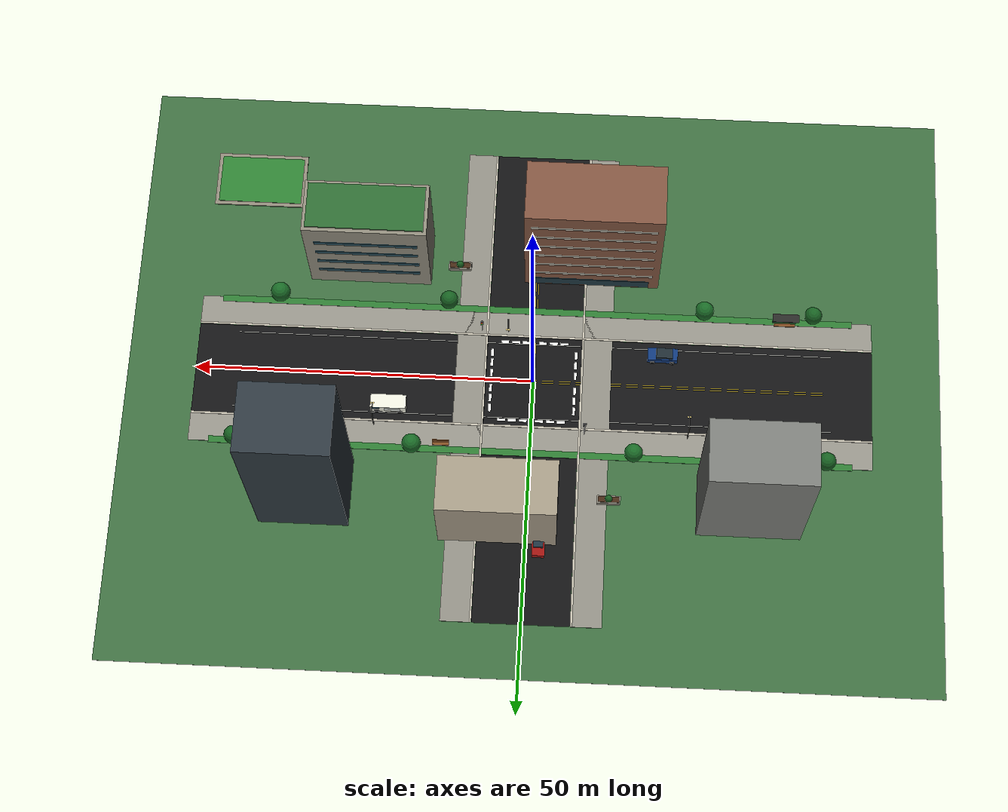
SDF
<?xml version="1.0" ?>
<sdf version="1.8">
  <!--
    city_street 世界：面向 Unitree Go2 城市道路/街区感知与行走测试的室外 Gazebo 场景。
    场景不依赖外部模型库，使用 SDF 基础几何构建高楼、道路、路缘、绿化、车辆和城市设施。
  -->
  <world name="city_street">
    <!-- 1 ms 物理步长适合四足机器人足端接触，静态城市几何主要提供碰撞和感知参照。 -->
    <physics name="1ms" type="bullet-featherstone">
      <max_step_size>0.001</max_step_size>
      <real_time_factor>1.0</real_time_factor>
      <real_time_update_rate>1000</real_time_update_rate>
    </physics>

    <!-- Gazebo Sim 系统插件：物理、传感器、用户命令、场景广播和接触检测。 -->
    <plugin filename="gz-sim-physics-system" name="gz::sim::systems::Physics"/>
    <plugin filename="gz-sim-sensors-system" name="gz::sim::systems::Sensors">
      <render_engine>ogre2</render_engine>
    </plugin>
    <plugin filename="gz-sim-user-commands-system" name="gz::sim::systems::UserCommands"/>
    <plugin filename="gz-sim-scene-broadcaster-system" name="gz::sim::systems::SceneBroadcaster"/>
    <plugin filename="gz-sim-contact-system" name="gz::sim::systems::Contact"/>

    <gravity>0 0 -9.8</gravity>
    <magnetic_field>5.5645e-06 2.28758e-05 -4.23884e-05</magnetic_field>
    <atmosphere type="adiabatic"/>

    <scene>
      <ambient>0.44 0.47 0.50 1</ambient>
      <background>0.68 0.76 0.86 1</background>
      <shadows>true</shadows>
    </scene>

    <gui fullscreen="0">
      <camera name="user_camera">
        <pose>36 -46 24 0 0.48 2.36</pose>
      </camera>
    </gui>

    <!-- 下午方向光，拉出建筑和行道树阴影，便于检查相机和激光点云层次。 -->
    <light type="directional" name="sun">
      <cast_shadows>true</cast_shadows>
      <pose>0 0 30 0 0 0</pose>
      <diffuse>0.92 0.88 0.78 1</diffuse>
      <specular>0.25 0.22 0.18 1</specular>
      <attenuation>
        <range>1000</range>
        <constant>0.9</constant>
        <linear>0.01</linear>
        <quadratic>0.001</quadratic>
      </attenuation>
      <direction>-0.55 0.35 -0.76</direction>
    </light>

    <!--
      城市底板：只用一个 z=0 的平面承担主要地面碰撞。
      道路、人行道铺装等薄层尽量作为视觉涂层，避免 Go2 足端被多层重叠 collision 卡住。
    -->
    <model name="city_ground">
      <static>true</static>
      <link name="link">
        <collision name="ground_collision">
          <geometry>
            <plane>
              <normal>0 0 1</normal>
              <size>120 90</size>
            </plane>
          </geometry>
          <surface>
            <friction>
              <ode>
                <mu>0.9</mu>
                <mu2>0.9</mu2>
              </ode>
            </friction>
          </surface>
        </collision>
        <visual name="ground_visual">
          <pose>0 0 -0.012 0 0 0</pose>
          <geometry>
            <box>
              <size>120 90 0.024</size>
            </box>
          </geometry>
          <material>
            <ambient>0.21 0.34 0.22 1</ambient>
            <diffuse>0.24 0.43 0.25 1</diffuse>
            <specular>0.03 0.04 0.03 1</specular>
          </material>
        </visual>
      </link>
      <pose>0 0 0 0 0 0</pose>
    </model>

    <!-- 主干路和十字路口。沥青只作为视觉薄层，碰撞由 city_ground 的平面提供。 -->
    <model name="asphalt_main_road">
      <static>true</static>
      <link name="link">
        <visual name="asphalt">
          <geometry>
            <box>
              <size>100 14 0.006</size>
            </box>
          </geometry>
          <material>
            <ambient>0.055 0.058 0.060 1</ambient>
            <diffuse>0.075 0.078 0.080 1</diffuse>
            <specular>0.08 0.08 0.08 1</specular>
          </material>
        </visual>
      </link>
      <pose>0 0 -0.002 0 0 0</pose>
    </model>

    <model name="asphalt_cross_road">
      <static>true</static>
      <link name="link">
        <visual name="asphalt">
          <geometry>
            <box>
              <size>14 74 0.006</size>
            </box>
          </geometry>
          <material>
            <ambient>0.052 0.055 0.058 1</ambient>
            <diffuse>0.070 0.073 0.076 1</diffuse>
            <specular>0.08 0.08 0.08 1</specular>
          </material>
        </visual>
      </link>
      <pose>0 0 -0.001 0 0 0</pose>
    </model>

    <!-- 混凝土人行道和路缘，高度给 Go2 一个真实的台阶/路边边界。 -->
    <model name="north_sidewalk">
      <static>true</static>
      <link name="link">
        <collision name="collision">
          <geometry>
            <box>
              <size>100 4.2 0.12</size>
            </box>
          </geometry>
        </collision>
        <visual name="concrete">
          <geometry>
            <box>
              <size>100 4.2 0.12</size>
            </box>
          </geometry>
          <material>
            <ambient>0.46 0.45 0.42 1</ambient>
            <diffuse>0.58 0.57 0.53 1</diffuse>
            <specular>0.08 0.08 0.07 1</specular>
          </material>
        </visual>
      </link>
      <pose>0 9.4 0.06 0 0 0</pose>
    </model>

    <model name="south_sidewalk">
      <static>true</static>
      <link name="link">
        <collision name="collision">
          <geometry>
            <box>
              <size>100 4.2 0.12</size>
            </box>
          </geometry>
        </collision>
        <visual name="concrete">
          <geometry>
            <box>
              <size>100 4.2 0.12</size>
            </box>
          </geometry>
          <material>
            <ambient>0.46 0.45 0.42 1</ambient>
            <diffuse>0.58 0.57 0.53 1</diffuse>
            <specular>0.08 0.08 0.07 1</specular>
          </material>
        </visual>
      </link>
      <pose>0 -9.4 0.06 0 0 0</pose>
    </model>

    <model name="east_sidewalk">
      <static>true</static>
      <link name="link">
        <collision name="collision">
          <geometry>
            <box>
              <size>4.2 74 0.12</size>
            </box>
          </geometry>
        </collision>
        <visual name="concrete">
          <geometry>
            <box>
              <size>4.2 74 0.12</size>
            </box>
          </geometry>
          <material>
            <ambient>0.45 0.44 0.41 1</ambient>
            <diffuse>0.56 0.55 0.51 1</diffuse>
            <specular>0.08 0.08 0.07 1</specular>
          </material>
        </visual>
      </link>
      <pose>9.4 0 0.06 0 0 0</pose>
    </model>

    <model name="west_sidewalk">
      <static>true</static>
      <link name="link">
        <collision name="collision">
          <geometry>
            <box>
              <size>4.2 74 0.12</size>
            </box>
          </geometry>
        </collision>
        <visual name="concrete">
          <geometry>
            <box>
              <size>4.2 74 0.12</size>
            </box>
          </geometry>
          <material>
            <ambient>0.45 0.44 0.41 1</ambient>
            <diffuse>0.56 0.55 0.51 1</diffuse>
            <specular>0.08 0.08 0.07 1</specular>
          </material>
        </visual>
      </link>
      <pose>-9.4 0 0.06 0 0 0</pose>
    </model>

    <model name="north_curb">
      <static>true</static>
      <link name="link">
        <collision name="collision">
          <geometry>
            <box>
              <size>100 0.28 0.18</size>
            </box>
          </geometry>
        </collision>
        <visual name="curb">
          <geometry>
            <box>
              <size>100 0.28 0.18</size>
            </box>
          </geometry>
          <material>
            <ambient>0.64 0.62 0.57 1</ambient>
            <diffuse>0.76 0.74 0.68 1</diffuse>
          </material>
        </visual>
      </link>
      <pose>0 7.16 0.09 0 0 0</pose>
    </model>

    <model name="south_curb">
      <static>true</static>
      <link name="link">
        <collision name="collision">
          <geometry>
            <box>
              <size>100 0.28 0.18</size>
            </box>
          </geometry>
        </collision>
        <visual name="curb">
          <geometry>
            <box>
              <size>100 0.28 0.18</size>
            </box>
          </geometry>
          <material>
            <ambient>0.64 0.62 0.57 1</ambient>
            <diffuse>0.76 0.74 0.68 1</diffuse>
          </material>
        </visual>
      </link>
      <pose>0 -7.16 0.09 0 0 0</pose>
    </model>

    <model name="east_curb">
      <static>true</static>
      <link name="link">
        <collision name="collision">
          <geometry>
            <box>
              <size>0.28 74 0.18</size>
            </box>
          </geometry>
        </collision>
        <visual name="curb">
          <geometry>
            <box>
              <size>0.28 74 0.18</size>
            </box>
          </geometry>
          <material>
            <ambient>0.64 0.62 0.57 1</ambient>
            <diffuse>0.76 0.74 0.68 1</diffuse>
          </material>
        </visual>
      </link>
      <pose>7.16 0 0.09 0 0 0</pose>
    </model>

    <model name="west_curb">
      <static>true</static>
      <link name="link">
        <collision name="collision">
          <geometry>
            <box>
              <size>0.28 74 0.18</size>
            </box>
          </geometry>
        </collision>
        <visual name="curb">
          <geometry>
            <box>
              <size>0.28 74 0.18</size>
            </box>
          </geometry>
          <material>
            <ambient>0.64 0.62 0.57 1</ambient>
            <diffuse>0.76 0.74 0.68 1</diffuse>
          </material>
        </visual>
      </link>
      <pose>-7.16 0 0.09 0 0 0</pose>
    </model>

    <!-- 道路标线、车道线、停止线和斑马线。 -->
    <model name="road_markings">
      <static>true</static>
      <link name="link">
        <visual name="double_yellow_left">
          <pose>0 0.18 0.032 0 0 0</pose>
          <geometry>
            <box>
              <size>86 0.08 0.012</size>
            </box>
          </geometry>
          <material>
            <ambient>0.95 0.74 0.12 1</ambient>
            <diffuse>1.00 0.82 0.16 1</diffuse>
          </material>
        </visual>
        <visual name="double_yellow_right">
          <pose>0 -0.18 0.032 0 0 0</pose>
          <geometry>
            <box>
              <size>86 0.08 0.012</size>
            </box>
          </geometry>
          <material>
            <ambient>0.95 0.74 0.12 1</ambient>
            <diffuse>1.00 0.82 0.16 1</diffuse>
          </material>
        </visual>
        <visual name="north_edge_line">
          <pose>0 5.9 0.032 0 0 0</pose>
          <geometry>
            <box>
              <size>88 0.10 0.012</size>
            </box>
          </geometry>
          <material>
            <ambient>0.86 0.86 0.82 1</ambient>
            <diffuse>0.96 0.96 0.92 1</diffuse>
          </material>
        </visual>
        <visual name="south_edge_line">
          <pose>0 -5.9 0.032 0 0 0</pose>
          <geometry>
            <box>
              <size>88 0.10 0.012</size>
            </box>
          </geometry>
          <material>
            <ambient>0.86 0.86 0.82 1</ambient>
            <diffuse>0.96 0.96 0.92 1</diffuse>
          </material>
        </visual>
        <visual name="cross_road_center_line_1">
          <pose>0.18 0 0.034 0 0 1.5708</pose>
          <geometry>
            <box>
              <size>60 0.08 0.012</size>
            </box>
          </geometry>
          <material>
            <ambient>0.95 0.74 0.12 1</ambient>
            <diffuse>1.00 0.82 0.16 1</diffuse>
          </material>
        </visual>
        <visual name="cross_road_center_line_2">
          <pose>-0.18 0 0.034 0 0 1.5708</pose>
          <geometry>
            <box>
              <size>60 0.08 0.012</size>
            </box>
          </geometry>
          <material>
            <ambient>0.95 0.74 0.12 1</ambient>
            <diffuse>1.00 0.82 0.16 1</diffuse>
          </material>
        </visual>
        <visual name="stop_line_west">
          <pose>-8.0 2.9 0.036 0 0 0</pose>
          <geometry>
            <box>
              <size>0.35 5.4 0.012</size>
            </box>
          </geometry>
          <material>
            <ambient>0.92 0.92 0.88 1</ambient>
            <diffuse>1.0 1.0 0.94 1</diffuse>
          </material>
        </visual>
        <visual name="stop_line_east">
          <pose>8.0 -2.9 0.036 0 0 0</pose>
          <geometry>
            <box>
              <size>0.35 5.4 0.012</size>
            </box>
          </geometry>
          <material>
            <ambient>0.92 0.92 0.88 1</ambient>
            <diffuse>1.0 1.0 0.94 1</diffuse>
          </material>
        </visual>
        <visual name="stop_line_north">
          <pose>-2.9 8.0 0.036 0 0 1.5708</pose>
          <geometry>
            <box>
              <size>0.35 5.4 0.012</size>
            </box>
          </geometry>
          <material>
            <ambient>0.92 0.92 0.88 1</ambient>
            <diffuse>1.0 1.0 0.94 1</diffuse>
          </material>
        </visual>
        <visual name="stop_line_south">
          <pose>2.9 -8.0 0.036 0 0 1.5708</pose>
          <geometry>
            <box>
              <size>0.35 5.4 0.012</size>
            </box>
          </geometry>
          <material>
            <ambient>0.92 0.92 0.88 1</ambient>
            <diffuse>1.0 1.0 0.94 1</diffuse>
          </material>
        </visual>
        <visual name="crosswalk_west_1">
          <pose>-6.2 -4.4 0.04 0 0 0</pose>
          <geometry>
            <box>
              <size>0.42 1.2 0.012</size>
            </box>
          </geometry>
          <material>
            <ambient>0.90 0.90 0.86 1</ambient>
            <diffuse>1.0 1.0 0.94 1</diffuse>
          </material>
        </visual>
        <visual name="crosswalk_west_2">
          <pose>-6.2 -2.8 0.04 0 0 0</pose>
          <geometry>
            <box>
              <size>0.42 1.2 0.012</size>
            </box>
          </geometry>
          <material>
            <ambient>0.90 0.90 0.86 1</ambient>
            <diffuse>1.0 1.0 0.94 1</diffuse>
          </material>
        </visual>
        <visual name="crosswalk_west_3">
          <pose>-6.2 -1.2 0.04 0 0 0</pose>
          <geometry>
            <box>
              <size>0.42 1.2 0.012</size>
            </box>
          </geometry>
          <material>
            <ambient>0.90 0.90 0.86 1</ambient>
            <diffuse>1.0 1.0 0.94 1</diffuse>
          </material>
        </visual>
        <visual name="crosswalk_west_4">
          <pose>-6.2 1.2 0.04 0 0 0</pose>
          <geometry>
            <box>
              <size>0.42 1.2 0.012</size>
            </box>
          </geometry>
          <material>
            <ambient>0.90 0.90 0.86 1</ambient>
            <diffuse>1.0 1.0 0.94 1</diffuse>
          </material>
        </visual>
        <visual name="crosswalk_west_5">
          <pose>-6.2 2.8 0.04 0 0 0</pose>
          <geometry>
            <box>
              <size>0.42 1.2 0.012</size>
            </box>
          </geometry>
          <material>
            <ambient>0.90 0.90 0.86 1</ambient>
            <diffuse>1.0 1.0 0.94 1</diffuse>
          </material>
        </visual>
        <visual name="crosswalk_west_6">
          <pose>-6.2 4.4 0.04 0 0 0</pose>
          <geometry>
            <box>
              <size>0.42 1.2 0.012</size>
            </box>
          </geometry>
          <material>
            <ambient>0.90 0.90 0.86 1</ambient>
            <diffuse>1.0 1.0 0.94 1</diffuse>
          </material>
        </visual>
        <visual name="crosswalk_east_1">
          <pose>6.2 -4.4 0.04 0 0 0</pose>
          <geometry>
            <box>
              <size>0.42 1.2 0.012</size>
            </box>
          </geometry>
          <material>
            <ambient>0.90 0.90 0.86 1</ambient>
            <diffuse>1.0 1.0 0.94 1</diffuse>
          </material>
        </visual>
        <visual name="crosswalk_east_2">
          <pose>6.2 -2.8 0.04 0 0 0</pose>
          <geometry>
            <box>
              <size>0.42 1.2 0.012</size>
            </box>
          </geometry>
          <material>
            <ambient>0.90 0.90 0.86 1</ambient>
            <diffuse>1.0 1.0 0.94 1</diffuse>
          </material>
        </visual>
        <visual name="crosswalk_east_3">
          <pose>6.2 -1.2 0.04 0 0 0</pose>
          <geometry>
            <box>
              <size>0.42 1.2 0.012</size>
            </box>
          </geometry>
          <material>
            <ambient>0.90 0.90 0.86 1</ambient>
            <diffuse>1.0 1.0 0.94 1</diffuse>
          </material>
        </visual>
        <visual name="crosswalk_east_4">
          <pose>6.2 1.2 0.04 0 0 0</pose>
          <geometry>
            <box>
              <size>0.42 1.2 0.012</size>
            </box>
          </geometry>
          <material>
            <ambient>0.90 0.90 0.86 1</ambient>
            <diffuse>1.0 1.0 0.94 1</diffuse>
          </material>
        </visual>
        <visual name="crosswalk_east_5">
          <pose>6.2 2.8 0.04 0 0 0</pose>
          <geometry>
            <box>
              <size>0.42 1.2 0.012</size>
            </box>
          </geometry>
          <material>
            <ambient>0.90 0.90 0.86 1</ambient>
            <diffuse>1.0 1.0 0.94 1</diffuse>
          </material>
        </visual>
        <visual name="crosswalk_east_6">
          <pose>6.2 4.4 0.04 0 0 0</pose>
          <geometry>
            <box>
              <size>0.42 1.2 0.012</size>
            </box>
          </geometry>
          <material>
            <ambient>0.90 0.90 0.86 1</ambient>
            <diffuse>1.0 1.0 0.94 1</diffuse>
          </material>
        </visual>
        <visual name="crosswalk_north_1">
          <pose>-4.4 6.2 0.04 0 0 1.5708</pose>
          <geometry>
            <box>
              <size>0.42 1.2 0.012</size>
            </box>
          </geometry>
          <material>
            <ambient>0.90 0.90 0.86 1</ambient>
            <diffuse>1.0 1.0 0.94 1</diffuse>
          </material>
        </visual>
        <visual name="crosswalk_north_2">
          <pose>-2.8 6.2 0.04 0 0 1.5708</pose>
          <geometry>
            <box>
              <size>0.42 1.2 0.012</size>
            </box>
          </geometry>
          <material>
            <ambient>0.90 0.90 0.86 1</ambient>
            <diffuse>1.0 1.0 0.94 1</diffuse>
          </material>
        </visual>
        <visual name="crosswalk_north_3">
          <pose>-1.2 6.2 0.04 0 0 1.5708</pose>
          <geometry>
            <box>
              <size>0.42 1.2 0.012</size>
            </box>
          </geometry>
          <material>
            <ambient>0.90 0.90 0.86 1</ambient>
            <diffuse>1.0 1.0 0.94 1</diffuse>
          </material>
        </visual>
        <visual name="crosswalk_north_4">
          <pose>1.2 6.2 0.04 0 0 1.5708</pose>
          <geometry>
            <box>
              <size>0.42 1.2 0.012</size>
            </box>
          </geometry>
          <material>
            <ambient>0.90 0.90 0.86 1</ambient>
            <diffuse>1.0 1.0 0.94 1</diffuse>
          </material>
        </visual>
        <visual name="crosswalk_north_5">
          <pose>2.8 6.2 0.04 0 0 1.5708</pose>
          <geometry>
            <box>
              <size>0.42 1.2 0.012</size>
            </box>
          </geometry>
          <material>
            <ambient>0.90 0.90 0.86 1</ambient>
            <diffuse>1.0 1.0 0.94 1</diffuse>
          </material>
        </visual>
        <visual name="crosswalk_north_6">
          <pose>4.4 6.2 0.04 0 0 1.5708</pose>
          <geometry>
            <box>
              <size>0.42 1.2 0.012</size>
            </box>
          </geometry>
          <material>
            <ambient>0.90 0.90 0.86 1</ambient>
            <diffuse>1.0 1.0 0.94 1</diffuse>
          </material>
        </visual>
        <visual name="crosswalk_south_1">
          <pose>-4.4 -6.2 0.04 0 0 1.5708</pose>
          <geometry>
            <box>
              <size>0.42 1.2 0.012</size>
            </box>
          </geometry>
          <material>
            <ambient>0.90 0.90 0.86 1</ambient>
            <diffuse>1.0 1.0 0.94 1</diffuse>
          </material>
        </visual>
        <visual name="crosswalk_south_2">
          <pose>-2.8 -6.2 0.04 0 0 1.5708</pose>
          <geometry>
            <box>
              <size>0.42 1.2 0.012</size>
            </box>
          </geometry>
          <material>
            <ambient>0.90 0.90 0.86 1</ambient>
            <diffuse>1.0 1.0 0.94 1</diffuse>
          </material>
        </visual>
        <visual name="crosswalk_south_3">
          <pose>-1.2 -6.2 0.04 0 0 1.5708</pose>
          <geometry>
            <box>
              <size>0.42 1.2 0.012</size>
            </box>
          </geometry>
          <material>
            <ambient>0.90 0.90 0.86 1</ambient>
            <diffuse>1.0 1.0 0.94 1</diffuse>
          </material>
        </visual>
        <visual name="crosswalk_south_4">
          <pose>1.2 -6.2 0.04 0 0 1.5708</pose>
          <geometry>
            <box>
              <size>0.42 1.2 0.012</size>
            </box>
          </geometry>
          <material>
            <ambient>0.90 0.90 0.86 1</ambient>
            <diffuse>1.0 1.0 0.94 1</diffuse>
          </material>
        </visual>
        <visual name="crosswalk_south_5">
          <pose>2.8 -6.2 0.04 0 0 1.5708</pose>
          <geometry>
            <box>
              <size>0.42 1.2 0.012</size>
            </box>
          </geometry>
          <material>
            <ambient>0.90 0.90 0.86 1</ambient>
            <diffuse>1.0 1.0 0.94 1</diffuse>
          </material>
        </visual>
        <visual name="crosswalk_south_6">
          <pose>4.4 -6.2 0.04 0 0 1.5708</pose>
          <geometry>
            <box>
              <size>0.42 1.2 0.012</size>
            </box>
          </geometry>
          <material>
            <ambient>0.90 0.90 0.86 1</ambient>
            <diffuse>1.0 1.0 0.94 1</diffuse>
          </material>
        </visual>
      </link>
    </model>

    <!-- 北侧高层办公楼，近路面有商铺玻璃和遮阳棚。 -->
    <model name="north_west_office_tower">
      <static>true</static>
      <pose>-32 18 0 0 0 0</pose>
      <link name="link">
        <collision name="building_collision">
          <pose>0 0 12 0 0 0</pose>
          <geometry>
            <box>
              <size>15 9 24</size>
            </box>
          </geometry>
        </collision>
        <visual name="concrete_mass">
          <pose>0 0 12 0 0 0</pose>
          <geometry>
            <box>
              <size>15 9 24</size>
            </box>
          </geometry>
          <material>
            <ambient>0.36 0.37 0.36 1</ambient>
            <diffuse>0.48 0.49 0.47 1</diffuse>
            <specular>0.12 0.12 0.11 1</specular>
          </material>
        </visual>
        <visual name="front_glass_01">
          <pose>-4.5 -4.56 4 0 0 0</pose>
          <geometry>
            <box>
              <size>2.8 0.08 0.9</size>
            </box>
          </geometry>
          <material>
            <ambient>0.10 0.18 0.24 1</ambient>
            <diffuse>0.14 0.28 0.38 1</diffuse>
            <specular>0.65 0.72 0.78 1</specular>
          </material>
        </visual>
        <visual name="front_glass_02">
          <pose>0 -4.56 4 0 0 0</pose>
          <geometry>
            <box>
              <size>2.8 0.08 0.9</size>
            </box>
          </geometry>
          <material>
            <ambient>0.10 0.18 0.24 1</ambient>
            <diffuse>0.14 0.28 0.38 1</diffuse>
            <specular>0.65 0.72 0.78 1</specular>
          </material>
        </visual>
        <visual name="front_glass_03">
          <pose>4.5 -4.56 4 0 0 0</pose>
          <geometry>
            <box>
              <size>2.8 0.08 0.9</size>
            </box>
          </geometry>
          <material>
            <ambient>0.10 0.18 0.24 1</ambient>
            <diffuse>0.14 0.28 0.38 1</diffuse>
            <specular>0.65 0.72 0.78 1</specular>
          </material>
        </visual>
        <visual name="front_glass_04">
          <pose>-4.5 -4.56 7 0 0 0</pose>
          <geometry>
            <box>
              <size>2.8 0.08 0.9</size>
            </box>
          </geometry>
          <material>
            <ambient>0.09 0.17 0.23 1</ambient>
            <diffuse>0.13 0.26 0.36 1</diffuse>
            <specular>0.62 0.70 0.76 1</specular>
          </material>
        </visual>
        <visual name="front_glass_05">
          <pose>0 -4.56 7 0 0 0</pose>
          <geometry>
            <box>
              <size>2.8 0.08 0.9</size>
            </box>
          </geometry>
          <material>
            <ambient>0.09 0.17 0.23 1</ambient>
            <diffuse>0.13 0.26 0.36 1</diffuse>
            <specular>0.62 0.70 0.76 1</specular>
          </material>
        </visual>
        <visual name="front_glass_06">
          <pose>4.5 -4.56 7 0 0 0</pose>
          <geometry>
            <box>
              <size>2.8 0.08 0.9</size>
            </box>
          </geometry>
          <material>
            <ambient>0.09 0.17 0.23 1</ambient>
            <diffuse>0.13 0.26 0.36 1</diffuse>
            <specular>0.62 0.70 0.76 1</specular>
          </material>
        </visual>
        <visual name="front_glass_07">
          <pose>-4.5 -4.56 10 0 0 0</pose>
          <geometry>
            <box>
              <size>2.8 0.08 0.9</size>
            </box>
          </geometry>
          <material>
            <ambient>0.09 0.17 0.23 1</ambient>
            <diffuse>0.13 0.26 0.36 1</diffuse>
            <specular>0.62 0.70 0.76 1</specular>
          </material>
        </visual>
        <visual name="front_glass_08">
          <pose>0 -4.56 10 0 0 0</pose>
          <geometry>
            <box>
              <size>2.8 0.08 0.9</size>
            </box>
          </geometry>
          <material>
            <ambient>0.09 0.17 0.23 1</ambient>
            <diffuse>0.13 0.26 0.36 1</diffuse>
            <specular>0.62 0.70 0.76 1</specular>
          </material>
        </visual>
        <visual name="front_glass_09">
          <pose>4.5 -4.56 10 0 0 0</pose>
          <geometry>
            <box>
              <size>2.8 0.08 0.9</size>
            </box>
          </geometry>
          <material>
            <ambient>0.09 0.17 0.23 1</ambient>
            <diffuse>0.13 0.26 0.36 1</diffuse>
            <specular>0.62 0.70 0.76 1</specular>
          </material>
        </visual>
        <visual name="front_glass_10">
          <pose>-4.5 -4.56 13 0 0 0</pose>
          <geometry>
            <box>
              <size>2.8 0.08 0.9</size>
            </box>
          </geometry>
          <material>
            <ambient>0.08 0.16 0.22 1</ambient>
            <diffuse>0.12 0.24 0.34 1</diffuse>
            <specular>0.58 0.68 0.75 1</specular>
          </material>
        </visual>
        <visual name="front_glass_11">
          <pose>0 -4.56 13 0 0 0</pose>
          <geometry>
            <box>
              <size>2.8 0.08 0.9</size>
            </box>
          </geometry>
          <material>
            <ambient>0.08 0.16 0.22 1</ambient>
            <diffuse>0.12 0.24 0.34 1</diffuse>
            <specular>0.58 0.68 0.75 1</specular>
          </material>
        </visual>
        <visual name="front_glass_12">
          <pose>4.5 -4.56 13 0 0 0</pose>
          <geometry>
            <box>
              <size>2.8 0.08 0.9</size>
            </box>
          </geometry>
          <material>
            <ambient>0.08 0.16 0.22 1</ambient>
            <diffuse>0.12 0.24 0.34 1</diffuse>
            <specular>0.58 0.68 0.75 1</specular>
          </material>
        </visual>
        <visual name="front_glass_13">
          <pose>-4.5 -4.56 16 0 0 0</pose>
          <geometry>
            <box>
              <size>2.8 0.08 0.9</size>
            </box>
          </geometry>
          <material>
            <ambient>0.08 0.16 0.22 1</ambient>
            <diffuse>0.12 0.24 0.34 1</diffuse>
            <specular>0.58 0.68 0.75 1</specular>
          </material>
        </visual>
        <visual name="front_glass_14">
          <pose>0 -4.56 16 0 0 0</pose>
          <geometry>
            <box>
              <size>2.8 0.08 0.9</size>
            </box>
          </geometry>
          <material>
            <ambient>0.08 0.16 0.22 1</ambient>
            <diffuse>0.12 0.24 0.34 1</diffuse>
            <specular>0.58 0.68 0.75 1</specular>
          </material>
        </visual>
        <visual name="front_glass_15">
          <pose>4.5 -4.56 16 0 0 0</pose>
          <geometry>
            <box>
              <size>2.8 0.08 0.9</size>
            </box>
          </geometry>
          <material>
            <ambient>0.08 0.16 0.22 1</ambient>
            <diffuse>0.12 0.24 0.34 1</diffuse>
            <specular>0.58 0.68 0.75 1</specular>
          </material>
        </visual>
        <visual name="front_glass_16">
          <pose>-4.5 -4.56 19 0 0 0</pose>
          <geometry>
            <box>
              <size>2.8 0.08 0.9</size>
            </box>
          </geometry>
          <material>
            <ambient>0.08 0.16 0.22 1</ambient>
            <diffuse>0.12 0.24 0.34 1</diffuse>
            <specular>0.58 0.68 0.75 1</specular>
          </material>
        </visual>
        <visual name="front_glass_17">
          <pose>0 -4.56 19 0 0 0</pose>
          <geometry>
            <box>
              <size>2.8 0.08 0.9</size>
            </box>
          </geometry>
          <material>
            <ambient>0.08 0.16 0.22 1</ambient>
            <diffuse>0.12 0.24 0.34 1</diffuse>
            <specular>0.58 0.68 0.75 1</specular>
          </material>
        </visual>
        <visual name="front_glass_18">
          <pose>4.5 -4.56 19 0 0 0</pose>
          <geometry>
            <box>
              <size>2.8 0.08 0.9</size>
            </box>
          </geometry>
          <material>
            <ambient>0.08 0.16 0.22 1</ambient>
            <diffuse>0.12 0.24 0.34 1</diffuse>
            <specular>0.58 0.68 0.75 1</specular>
          </material>
        </visual>
        <visual name="front_glass_19">
          <pose>-4.5 -4.56 22 0 0 0</pose>
          <geometry>
            <box>
              <size>2.8 0.08 0.9</size>
            </box>
          </geometry>
          <material>
            <ambient>0.08 0.16 0.22 1</ambient>
            <diffuse>0.12 0.24 0.34 1</diffuse>
            <specular>0.58 0.68 0.75 1</specular>
          </material>
        </visual>
        <visual name="front_glass_20">
          <pose>0 -4.56 22 0 0 0</pose>
          <geometry>
            <box>
              <size>2.8 0.08 0.9</size>
            </box>
          </geometry>
          <material>
            <ambient>0.08 0.16 0.22 1</ambient>
            <diffuse>0.12 0.24 0.34 1</diffuse>
            <specular>0.58 0.68 0.75 1</specular>
          </material>
        </visual>
        <visual name="front_glass_21">
          <pose>4.5 -4.56 22 0 0 0</pose>
          <geometry>
            <box>
              <size>2.8 0.08 0.9</size>
            </box>
          </geometry>
          <material>
            <ambient>0.08 0.16 0.22 1</ambient>
            <diffuse>0.12 0.24 0.34 1</diffuse>
            <specular>0.58 0.68 0.75 1</specular>
          </material>
        </visual>
        <visual name="shopfront">
          <pose>0 -4.62 1.35 0 0 0</pose>
          <geometry>
            <box>
              <size>12.5 0.10 1.9</size>
            </box>
          </geometry>
          <material>
            <ambient>0.08 0.11 0.13 1</ambient>
            <diffuse>0.12 0.18 0.20 1</diffuse>
            <specular>0.80 0.82 0.82 1</specular>
          </material>
        </visual>
        <visual name="awning">
          <pose>0 -5.05 2.55 0 0 0</pose>
          <geometry>
            <box>
              <size>13.0 0.9 0.25</size>
            </box>
          </geometry>
          <material>
            <ambient>0.42 0.05 0.04 1</ambient>
            <diffuse>0.62 0.08 0.06 1</diffuse>
          </material>
        </visual>
      </link>
    </model>

    <model name="north_east_glass_tower">
      <static>true</static>
      <pose>32 18.5 0 0 0 0</pose>
      <link name="link">
        <collision name="collision">
          <pose>0 0 15 0 0 0</pose>
          <geometry>
            <box>
              <size>13 10 30</size>
            </box>
          </geometry>
        </collision>
        <visual name="dark_core">
          <pose>0 0 15 0 0 0</pose>
          <geometry>
            <box>
              <size>13 10 30</size>
            </box>
          </geometry>
          <material>
            <ambient>0.13 0.16 0.18 1</ambient>
            <diffuse>0.18 0.22 0.25 1</diffuse>
            <specular>0.30 0.34 0.36 1</specular>
          </material>
        </visual>
        <visual name="front_glass_grid_1">
          <pose>-3.7 -5.06 4 0 0 0</pose>
          <geometry>
            <box>
              <size>2.3 0.08 1.1</size>
            </box>
          </geometry>
          <material>
            <ambient>0.09 0.20 0.27 1</ambient>
            <diffuse>0.16 0.34 0.45 1</diffuse>
            <specular>0.70 0.76 0.82 1</specular>
          </material>
        </visual>
        <visual name="front_glass_grid_2">
          <pose>0 -5.06 4 0 0 0</pose>
          <geometry>
            <box>
              <size>2.3 0.08 1.1</size>
            </box>
          </geometry>
          <material>
            <ambient>0.09 0.20 0.27 1</ambient>
            <diffuse>0.16 0.34 0.45 1</diffuse>
            <specular>0.70 0.76 0.82 1</specular>
          </material>
        </visual>
        <visual name="front_glass_grid_3">
          <pose>3.7 -5.06 4 0 0 0</pose>
          <geometry>
            <box>
              <size>2.3 0.08 1.1</size>
            </box>
          </geometry>
          <material>
            <ambient>0.09 0.20 0.27 1</ambient>
            <diffuse>0.16 0.34 0.45 1</diffuse>
            <specular>0.70 0.76 0.82 1</specular>
          </material>
        </visual>
        <visual name="front_glass_grid_4">
          <pose>-3.7 -5.06 8 0 0 0</pose>
          <geometry>
            <box>
              <size>2.3 0.08 1.1</size>
            </box>
          </geometry>
          <material>
            <ambient>0.09 0.20 0.27 1</ambient>
            <diffuse>0.16 0.34 0.45 1</diffuse>
            <specular>0.70 0.76 0.82 1</specular>
          </material>
        </visual>
        <visual name="front_glass_grid_5">
          <pose>0 -5.06 8 0 0 0</pose>
          <geometry>
            <box>
              <size>2.3 0.08 1.1</size>
            </box>
          </geometry>
          <material>
            <ambient>0.09 0.20 0.27 1</ambient>
            <diffuse>0.16 0.34 0.45 1</diffuse>
            <specular>0.70 0.76 0.82 1</specular>
          </material>
        </visual>
        <visual name="front_glass_grid_6">
          <pose>3.7 -5.06 8 0 0 0</pose>
          <geometry>
            <box>
              <size>2.3 0.08 1.1</size>
            </box>
          </geometry>
          <material>
            <ambient>0.09 0.20 0.27 1</ambient>
            <diffuse>0.16 0.34 0.45 1</diffuse>
            <specular>0.70 0.76 0.82 1</specular>
          </material>
        </visual>
        <visual name="front_glass_grid_7">
          <pose>-3.7 -5.06 12 0 0 0</pose>
          <geometry>
            <box>
              <size>2.3 0.08 1.1</size>
            </box>
          </geometry>
          <material>
            <ambient>0.09 0.20 0.27 1</ambient>
            <diffuse>0.16 0.34 0.45 1</diffuse>
            <specular>0.70 0.76 0.82 1</specular>
          </material>
        </visual>
        <visual name="front_glass_grid_8">
          <pose>0 -5.06 12 0 0 0</pose>
          <geometry>
            <box>
              <size>2.3 0.08 1.1</size>
            </box>
          </geometry>
          <material>
            <ambient>0.09 0.20 0.27 1</ambient>
            <diffuse>0.16 0.34 0.45 1</diffuse>
            <specular>0.70 0.76 0.82 1</specular>
          </material>
        </visual>
        <visual name="front_glass_grid_9">
          <pose>3.7 -5.06 12 0 0 0</pose>
          <geometry>
            <box>
              <size>2.3 0.08 1.1</size>
            </box>
          </geometry>
          <material>
            <ambient>0.09 0.20 0.27 1</ambient>
            <diffuse>0.16 0.34 0.45 1</diffuse>
            <specular>0.70 0.76 0.82 1</specular>
          </material>
        </visual>
        <visual name="front_glass_grid_10">
          <pose>-3.7 -5.06 16 0 0 0</pose>
          <geometry>
            <box>
              <size>2.3 0.08 1.1</size>
            </box>
          </geometry>
          <material>
            <ambient>0.08 0.19 0.26 1</ambient>
            <diffuse>0.15 0.32 0.43 1</diffuse>
            <specular>0.70 0.76 0.82 1</specular>
          </material>
        </visual>
        <visual name="front_glass_grid_11">
          <pose>0 -5.06 16 0 0 0</pose>
          <geometry>
            <box>
              <size>2.3 0.08 1.1</size>
            </box>
          </geometry>
          <material>
            <ambient>0.08 0.19 0.26 1</ambient>
            <diffuse>0.15 0.32 0.43 1</diffuse>
            <specular>0.70 0.76 0.82 1</specular>
          </material>
        </visual>
        <visual name="front_glass_grid_12">
          <pose>3.7 -5.06 16 0 0 0</pose>
          <geometry>
            <box>
              <size>2.3 0.08 1.1</size>
            </box>
          </geometry>
          <material>
            <ambient>0.08 0.19 0.26 1</ambient>
            <diffuse>0.15 0.32 0.43 1</diffuse>
            <specular>0.70 0.76 0.82 1</specular>
          </material>
        </visual>
        <visual name="front_glass_grid_13">
          <pose>-3.7 -5.06 20 0 0 0</pose>
          <geometry>
            <box>
              <size>2.3 0.08 1.1</size>
            </box>
          </geometry>
          <material>
            <ambient>0.08 0.19 0.26 1</ambient>
            <diffuse>0.15 0.32 0.43 1</diffuse>
            <specular>0.70 0.76 0.82 1</specular>
          </material>
        </visual>
        <visual name="front_glass_grid_14">
          <pose>0 -5.06 20 0 0 0</pose>
          <geometry>
            <box>
              <size>2.3 0.08 1.1</size>
            </box>
          </geometry>
          <material>
            <ambient>0.08 0.19 0.26 1</ambient>
            <diffuse>0.15 0.32 0.43 1</diffuse>
            <specular>0.70 0.76 0.82 1</specular>
          </material>
        </visual>
        <visual name="front_glass_grid_15">
          <pose>3.7 -5.06 20 0 0 0</pose>
          <geometry>
            <box>
              <size>2.3 0.08 1.1</size>
            </box>
          </geometry>
          <material>
            <ambient>0.08 0.19 0.26 1</ambient>
            <diffuse>0.15 0.32 0.43 1</diffuse>
            <specular>0.70 0.76 0.82 1</specular>
          </material>
        </visual>
        <visual name="front_glass_grid_16">
          <pose>-3.7 -5.06 24 0 0 0</pose>
          <geometry>
            <box>
              <size>2.3 0.08 1.1</size>
            </box>
          </geometry>
          <material>
            <ambient>0.08 0.19 0.26 1</ambient>
            <diffuse>0.15 0.32 0.43 1</diffuse>
            <specular>0.70 0.76 0.82 1</specular>
          </material>
        </visual>
        <visual name="front_glass_grid_17">
          <pose>0 -5.06 24 0 0 0</pose>
          <geometry>
            <box>
              <size>2.3 0.08 1.1</size>
            </box>
          </geometry>
          <material>
            <ambient>0.08 0.19 0.26 1</ambient>
            <diffuse>0.15 0.32 0.43 1</diffuse>
            <specular>0.70 0.76 0.82 1</specular>
          </material>
        </visual>
        <visual name="front_glass_grid_18">
          <pose>3.7 -5.06 24 0 0 0</pose>
          <geometry>
            <box>
              <size>2.3 0.08 1.1</size>
            </box>
          </geometry>
          <material>
            <ambient>0.08 0.19 0.26 1</ambient>
            <diffuse>0.15 0.32 0.43 1</diffuse>
            <specular>0.70 0.76 0.82 1</specular>
          </material>
        </visual>
        <visual name="front_glass_grid_19">
          <pose>-3.7 -5.06 28 0 0 0</pose>
          <geometry>
            <box>
              <size>2.3 0.08 1.1</size>
            </box>
          </geometry>
          <material>
            <ambient>0.08 0.19 0.26 1</ambient>
            <diffuse>0.15 0.32 0.43 1</diffuse>
            <specular>0.70 0.76 0.82 1</specular>
          </material>
        </visual>
        <visual name="front_glass_grid_20">
          <pose>0 -5.06 28 0 0 0</pose>
          <geometry>
            <box>
              <size>2.3 0.08 1.1</size>
            </box>
          </geometry>
          <material>
            <ambient>0.08 0.19 0.26 1</ambient>
            <diffuse>0.15 0.32 0.43 1</diffuse>
            <specular>0.70 0.76 0.82 1</specular>
          </material>
        </visual>
        <visual name="front_glass_grid_21">
          <pose>3.7 -5.06 28 0 0 0</pose>
          <geometry>
            <box>
              <size>2.3 0.08 1.1</size>
            </box>
          </geometry>
          <material>
            <ambient>0.08 0.19 0.26 1</ambient>
            <diffuse>0.15 0.32 0.43 1</diffuse>
            <specular>0.70 0.76 0.82 1</specular>
          </material>
        </visual>
      </link>
    </model>

    <model name="south_mid_apartment_block">
      <static>true</static>
      <pose>-8 -20.5 0 0 0 0</pose>
      <link name="link">
        <collision name="collision">
          <pose>0 0 11 0 0 0</pose>
          <geometry>
            <box>
              <size>20 9 22</size>
            </box>
          </geometry>
        </collision>
        <visual name="brick_mass">
          <pose>0 0 11 0 0 0</pose>
          <geometry>
            <box>
              <size>20 9 22</size>
            </box>
          </geometry>
          <material>
            <ambient>0.37 0.24 0.18 1</ambient>
            <diffuse>0.50 0.33 0.25 1</diffuse>
            <specular>0.06 0.05 0.04 1</specular>
          </material>
        </visual>
        <visual name="balcony_band_01">
          <pose>0 4.56 4 0 0 0</pose>
          <geometry>
            <box>
              <size>18 0.12 0.35</size>
            </box>
          </geometry>
          <material>
            <ambient>0.75 0.74 0.68 1</ambient>
            <diffuse>0.85 0.84 0.78 1</diffuse>
          </material>
        </visual>
        <visual name="balcony_band_02">
          <pose>0 4.56 7 0 0 0</pose>
          <geometry>
            <box>
              <size>18 0.12 0.35</size>
            </box>
          </geometry>
          <material>
            <ambient>0.75 0.74 0.68 1</ambient>
            <diffuse>0.85 0.84 0.78 1</diffuse>
          </material>
        </visual>
        <visual name="balcony_band_03">
          <pose>0 4.56 10 0 0 0</pose>
          <geometry>
            <box>
              <size>18 0.12 0.35</size>
            </box>
          </geometry>
          <material>
            <ambient>0.75 0.74 0.68 1</ambient>
            <diffuse>0.85 0.84 0.78 1</diffuse>
          </material>
        </visual>
        <visual name="balcony_band_04">
          <pose>0 4.56 13 0 0 0</pose>
          <geometry>
            <box>
              <size>18 0.12 0.35</size>
            </box>
          </geometry>
          <material>
            <ambient>0.75 0.74 0.68 1</ambient>
            <diffuse>0.85 0.84 0.78 1</diffuse>
          </material>
        </visual>
        <visual name="balcony_band_05">
          <pose>0 4.56 16 0 0 0</pose>
          <geometry>
            <box>
              <size>18 0.12 0.35</size>
            </box>
          </geometry>
          <material>
            <ambient>0.75 0.74 0.68 1</ambient>
            <diffuse>0.85 0.84 0.78 1</diffuse>
          </material>
        </visual>
        <visual name="balcony_band_06">
          <pose>0 4.56 19 0 0 0</pose>
          <geometry>
            <box>
              <size>18 0.12 0.35</size>
            </box>
          </geometry>
          <material>
            <ambient>0.75 0.74 0.68 1</ambient>
            <diffuse>0.85 0.84 0.78 1</diffuse>
          </material>
        </visual>
        <visual name="shop_windows">
          <pose>0 4.62 1.4 0 0 0</pose>
          <geometry>
            <box>
              <size>17 0.10 1.8</size>
            </box>
          </geometry>
          <material>
            <ambient>0.08 0.13 0.16 1</ambient>
            <diffuse>0.12 0.22 0.26 1</diffuse>
            <specular>0.65 0.70 0.72 1</specular>
          </material>
        </visual>
      </link>
    </model>

    <model name="south_east_mixed_use_block">
      <static>true</static>
      <pose>25 -19 0 0 0 0</pose>
      <link name="link">
        <collision name="collision">
          <pose>0 0 8.5 0 0 0</pose>
          <geometry>
            <box>
              <size>18 8 17</size>
            </box>
          </geometry>
        </collision>
        <visual name="stone_mass">
          <pose>0 0 8.5 0 0 0</pose>
          <geometry>
            <box>
              <size>18 8 17</size>
            </box>
          </geometry>
          <material>
            <ambient>0.42 0.40 0.35 1</ambient>
            <diffuse>0.56 0.54 0.48 1</diffuse>
            <specular>0.08 0.08 0.07 1</specular>
          </material>
        </visual>
        <visual name="window_strip_01">
          <pose>0 4.06 4 0 0 0</pose>
          <geometry>
            <box>
              <size>15 0.08 0.75</size>
            </box>
          </geometry>
          <material>
            <ambient>0.09 0.17 0.21 1</ambient>
            <diffuse>0.14 0.28 0.33 1</diffuse>
            <specular>0.58 0.65 0.70 1</specular>
          </material>
        </visual>
        <visual name="window_strip_02">
          <pose>0 4.06 7 0 0 0</pose>
          <geometry>
            <box>
              <size>15 0.08 0.75</size>
            </box>
          </geometry>
          <material>
            <ambient>0.09 0.17 0.21 1</ambient>
            <diffuse>0.14 0.28 0.33 1</diffuse>
            <specular>0.58 0.65 0.70 1</specular>
          </material>
        </visual>
        <visual name="window_strip_03">
          <pose>0 4.06 10 0 0 0</pose>
          <geometry>
            <box>
              <size>15 0.08 0.75</size>
            </box>
          </geometry>
          <material>
            <ambient>0.09 0.17 0.21 1</ambient>
            <diffuse>0.14 0.28 0.33 1</diffuse>
            <specular>0.58 0.65 0.70 1</specular>
          </material>
        </visual>
        <visual name="window_strip_04">
          <pose>0 4.06 13 0 0 0</pose>
          <geometry>
            <box>
              <size>15 0.08 0.75</size>
            </box>
          </geometry>
          <material>
            <ambient>0.09 0.17 0.21 1</ambient>
            <diffuse>0.14 0.28 0.33 1</diffuse>
            <specular>0.58 0.65 0.70 1</specular>
          </material>
        </visual>
        <visual name="green_roof">
          <pose>0 0 17.18 0 0 0</pose>
          <geometry>
            <box>
              <size>17 7 0.25</size>
            </box>
          </geometry>
          <material>
            <ambient>0.12 0.28 0.13 1</ambient>
            <diffuse>0.18 0.42 0.20 1</diffuse>
          </material>
        </visual>
      </link>
    </model>

    <model name="north_center_civic_building">
      <static>true</static>
      <pose>4 21 0 0 0 0</pose>
      <link name="link">
        <collision name="collision">
          <pose>0 0 7 0 0 0</pose>
          <geometry>
            <box>
              <size>17 8 14</size>
            </box>
          </geometry>
        </collision>
        <visual name="facade">
          <pose>0 0 7 0 0 0</pose>
          <geometry>
            <box>
              <size>17 8 14</size>
            </box>
          </geometry>
          <material>
            <ambient>0.50 0.47 0.40 1</ambient>
            <diffuse>0.64 0.60 0.52 1</diffuse>
            <specular>0.08 0.08 0.07 1</specular>
          </material>
        </visual>
        <visual name="column_01">
          <pose>-6 -4.25 2.6 0 0 0</pose>
          <geometry>
            <cylinder>
              <radius>0.24</radius>
              <length>5.2</length>
            </cylinder>
          </geometry>
          <material>
            <ambient>0.80 0.78 0.70 1</ambient>
            <diffuse>0.90 0.88 0.80 1</diffuse>
          </material>
        </visual>
        <visual name="column_02">
          <pose>-2 -4.25 2.6 0 0 0</pose>
          <geometry>
            <cylinder>
              <radius>0.24</radius>
              <length>5.2</length>
            </cylinder>
          </geometry>
          <material>
            <ambient>0.80 0.78 0.70 1</ambient>
            <diffuse>0.90 0.88 0.80 1</diffuse>
          </material>
        </visual>
        <visual name="column_03">
          <pose>2 -4.25 2.6 0 0 0</pose>
          <geometry>
            <cylinder>
              <radius>0.24</radius>
              <length>5.2</length>
            </cylinder>
          </geometry>
          <material>
            <ambient>0.80 0.78 0.70 1</ambient>
            <diffuse>0.90 0.88 0.80 1</diffuse>
          </material>
        </visual>
        <visual name="column_04">
          <pose>6 -4.25 2.6 0 0 0</pose>
          <geometry>
            <cylinder>
              <radius>0.24</radius>
              <length>5.2</length>
            </cylinder>
          </geometry>
          <material>
            <ambient>0.80 0.78 0.70 1</ambient>
            <diffuse>0.90 0.88 0.80 1</diffuse>
          </material>
        </visual>
        <visual name="upper_window_band">
          <pose>0 -4.06 9.3 0 0 0</pose>
          <geometry>
            <box>
              <size>13 0.08 1.0</size>
            </box>
          </geometry>
          <material>
            <ambient>0.10 0.17 0.20 1</ambient>
            <diffuse>0.15 0.26 0.31 1</diffuse>
            <specular>0.55 0.60 0.65 1</specular>
          </material>
        </visual>
      </link>
    </model>

    <!-- 道路两侧绿化带和口袋公园。 -->
    <model name="north_green_strip">
      <static>true</static>
      <link name="link">
        <visual name="grass">
          <geometry>
            <box>
              <size>94 1.0 0.06</size>
            </box>
          </geometry>
          <material>
            <ambient>0.12 0.32 0.14 1</ambient>
            <diffuse>0.18 0.48 0.20 1</diffuse>
          </material>
        </visual>
      </link>
      <pose>0 11.25 0.12 0 0 0</pose>
    </model>

    <model name="south_green_strip">
      <static>true</static>
      <link name="link">
        <visual name="grass">
          <geometry>
            <box>
              <size>94 1.0 0.06</size>
            </box>
          </geometry>
          <material>
            <ambient>0.12 0.32 0.14 1</ambient>
            <diffuse>0.18 0.48 0.20 1</diffuse>
          </material>
        </visual>
      </link>
      <pose>0 -11.25 0.12 0 0 0</pose>
    </model>

    <model name="pocket_park">
      <static>true</static>
      <pose>43 -31 0 0 0 0</pose>
      <link name="link">
        <collision name="low_wall_collision">
          <pose>0 0 0.25 0 0 0</pose>
          <geometry>
            <box>
              <size>13 8 0.5</size>
            </box>
          </geometry>
        </collision>
        <visual name="grass_square">
          <pose>0 0 0.08 0 0 0</pose>
          <geometry>
            <box>
              <size>13 8 0.12</size>
            </box>
          </geometry>
          <material>
            <ambient>0.10 0.28 0.13 1</ambient>
            <diffuse>0.17 0.42 0.19 1</diffuse>
          </material>
        </visual>
        <visual name="edge_wall">
          <pose>0 0 0.32 0 0 0</pose>
          <geometry>
            <box>
              <size>13.6 8.6 0.2</size>
            </box>
          </geometry>
          <material>
            <ambient>0.44 0.41 0.36 1</ambient>
            <diffuse>0.56 0.53 0.47 1</diffuse>
          </material>
        </visual>
        <visual name="inner_grass">
          <pose>0 0 0.45 0 0 0</pose>
          <geometry>
            <box>
              <size>12.5 7.5 0.08</size>
            </box>
          </geometry>
          <material>
            <ambient>0.10 0.32 0.12 1</ambient>
            <diffuse>0.18 0.50 0.20 1</diffuse>
          </material>
        </visual>
      </link>
    </model>

    <!-- 行道树：圆柱树干和低多边形球形树冠，给激光雷达提供自然散乱轮廓。 -->
    <model name="tree_north_01">
      <static>true</static>
      <pose>-43 11.4 0 0 0 0</pose>
      <link name="link">
        <collision name="trunk_collision">
          <pose>0 0 1.05 0 0 0</pose>
          <geometry>
            <cylinder>
              <radius>0.22</radius>
              <length>2.1</length>
            </cylinder>
          </geometry>
        </collision>
        <visual name="trunk">
          <pose>0 0 1.05 0 0 0</pose>
          <geometry>
            <cylinder>
              <radius>0.22</radius>
              <length>2.1</length>
            </cylinder>
          </geometry>
          <material>
            <ambient>0.24 0.13 0.07 1</ambient>
            <diffuse>0.36 0.20 0.10 1</diffuse>
          </material>
        </visual>
        <visual name="canopy">
          <pose>0 0 2.85 0 0 0</pose>
          <geometry>
            <sphere>
              <radius>1.35</radius>
            </sphere>
          </geometry>
          <material>
            <ambient>0.05 0.24 0.08 1</ambient>
            <diffuse>0.09 0.38 0.13 1</diffuse>
            <specular>0.03 0.06 0.03 1</specular>
          </material>
        </visual>
      </link>
    </model>

    <model name="tree_north_02">
      <static>true</static>
      <pose>-29 11.4 0 0 0 0</pose>
      <link name="link">
        <collision name="trunk_collision">
          <pose>0 0 1.05 0 0 0</pose>
          <geometry>
            <cylinder>
              <radius>0.22</radius>
              <length>2.1</length>
            </cylinder>
          </geometry>
        </collision>
        <visual name="trunk">
          <pose>0 0 1.05 0 0 0</pose>
          <geometry>
            <cylinder>
              <radius>0.22</radius>
              <length>2.1</length>
            </cylinder>
          </geometry>
          <material>
            <ambient>0.24 0.13 0.07 1</ambient>
            <diffuse>0.36 0.20 0.10 1</diffuse>
          </material>
        </visual>
        <visual name="canopy">
          <pose>0.15 -0.1 2.85 0 0 0</pose>
          <geometry>
            <sphere>
              <radius>1.45</radius>
            </sphere>
          </geometry>
          <material>
            <ambient>0.05 0.24 0.08 1</ambient>
            <diffuse>0.09 0.38 0.13 1</diffuse>
          </material>
        </visual>
      </link>
    </model>

    <model name="tree_north_03">
      <static>true</static>
      <pose>-15 11.4 0 0 0 0</pose>
      <link name="link">
        <collision name="trunk_collision">
          <pose>0 0 1.05 0 0 0</pose>
          <geometry>
            <cylinder>
              <radius>0.22</radius>
              <length>2.1</length>
            </cylinder>
          </geometry>
        </collision>
        <visual name="trunk">
          <pose>0 0 1.05 0 0 0</pose>
          <geometry>
            <cylinder>
              <radius>0.22</radius>
              <length>2.1</length>
            </cylinder>
          </geometry>
          <material>
            <ambient>0.24 0.13 0.07 1</ambient>
            <diffuse>0.36 0.20 0.10 1</diffuse>
          </material>
        </visual>
        <visual name="canopy">
          <pose>-0.1 0.05 2.9 0 0 0</pose>
          <geometry>
            <sphere>
              <radius>1.35</radius>
            </sphere>
          </geometry>
          <material>
            <ambient>0.06 0.26 0.09 1</ambient>
            <diffuse>0.10 0.42 0.15 1</diffuse>
          </material>
        </visual>
      </link>
    </model>

    <model name="tree_north_04">
      <static>true</static>
      <pose>17 11.4 0 0 0 0</pose>
      <link name="link">
        <collision name="trunk_collision">
          <pose>0 0 1.05 0 0 0</pose>
          <geometry>
            <cylinder>
              <radius>0.22</radius>
              <length>2.1</length>
            </cylinder>
          </geometry>
        </collision>
        <visual name="trunk">
          <pose>0 0 1.05 0 0 0</pose>
          <geometry>
            <cylinder>
              <radius>0.22</radius>
              <length>2.1</length>
            </cylinder>
          </geometry>
          <material>
            <ambient>0.24 0.13 0.07 1</ambient>
            <diffuse>0.36 0.20 0.10 1</diffuse>
          </material>
        </visual>
        <visual name="canopy">
          <pose>0.1 0.1 2.9 0 0 0</pose>
          <geometry>
            <sphere>
              <radius>1.4</radius>
            </sphere>
          </geometry>
          <material>
            <ambient>0.06 0.26 0.09 1</ambient>
            <diffuse>0.10 0.42 0.15 1</diffuse>
          </material>
        </visual>
      </link>
    </model>

    <model name="tree_north_05">
      <static>true</static>
      <pose>43 11.4 0 0 0 0</pose>
      <link name="link">
        <collision name="trunk_collision">
          <pose>0 0 1.05 0 0 0</pose>
          <geometry>
            <cylinder>
              <radius>0.22</radius>
              <length>2.1</length>
            </cylinder>
          </geometry>
        </collision>
        <visual name="trunk">
          <pose>0 0 1.05 0 0 0</pose>
          <geometry>
            <cylinder>
              <radius>0.22</radius>
              <length>2.1</length>
            </cylinder>
          </geometry>
          <material>
            <ambient>0.24 0.13 0.07 1</ambient>
            <diffuse>0.36 0.20 0.10 1</diffuse>
          </material>
        </visual>
        <visual name="canopy">
          <pose>0 0 2.85 0 0 0</pose>
          <geometry>
            <sphere>
              <radius>1.35</radius>
            </sphere>
          </geometry>
          <material>
            <ambient>0.05 0.24 0.08 1</ambient>
            <diffuse>0.09 0.38 0.13 1</diffuse>
          </material>
        </visual>
      </link>
    </model>

    <model name="tree_south_01">
      <static>true</static>
      <pose>-41 -11.4 0 0 0 0</pose>
      <link name="link">
        <collision name="trunk_collision">
          <pose>0 0 1.05 0 0 0</pose>
          <geometry>
            <cylinder>
              <radius>0.22</radius>
              <length>2.1</length>
            </cylinder>
          </geometry>
        </collision>
        <visual name="trunk">
          <pose>0 0 1.05 0 0 0</pose>
          <geometry>
            <cylinder>
              <radius>0.22</radius>
              <length>2.1</length>
            </cylinder>
          </geometry>
          <material>
            <ambient>0.24 0.13 0.07 1</ambient>
            <diffuse>0.36 0.20 0.10 1</diffuse>
          </material>
        </visual>
        <visual name="canopy">
          <pose>0 0 2.75 0 0 0</pose>
          <geometry>
            <sphere>
              <radius>1.30</radius>
            </sphere>
          </geometry>
          <material>
            <ambient>0.05 0.24 0.08 1</ambient>
            <diffuse>0.09 0.38 0.13 1</diffuse>
          </material>
        </visual>
      </link>
    </model>

    <model name="tree_south_02">
      <static>true</static>
      <pose>-25 -11.4 0 0 0 0</pose>
      <link name="link">
        <collision name="trunk_collision">
          <pose>0 0 1.05 0 0 0</pose>
          <geometry>
            <cylinder>
              <radius>0.22</radius>
              <length>2.1</length>
            </cylinder>
          </geometry>
        </collision>
        <visual name="trunk">
          <pose>0 0 1.05 0 0 0</pose>
          <geometry>
            <cylinder>
              <radius>0.22</radius>
              <length>2.1</length>
            </cylinder>
          </geometry>
          <material>
            <ambient>0.24 0.13 0.07 1</ambient>
            <diffuse>0.36 0.20 0.10 1</diffuse>
          </material>
        </visual>
        <visual name="canopy">
          <pose>0.1 0.05 2.9 0 0 0</pose>
          <geometry>
            <sphere>
              <radius>1.4</radius>
            </sphere>
          </geometry>
          <material>
            <ambient>0.06 0.26 0.09 1</ambient>
            <diffuse>0.10 0.42 0.15 1</diffuse>
          </material>
        </visual>
      </link>
    </model>

    <model name="tree_south_03">
      <static>true</static>
      <pose>13 -11.4 0 0 0 0</pose>
      <link name="link">
        <collision name="trunk_collision">
          <pose>0 0 1.05 0 0 0</pose>
          <geometry>
            <cylinder>
              <radius>0.22</radius>
              <length>2.1</length>
            </cylinder>
          </geometry>
        </collision>
        <visual name="trunk">
          <pose>0 0 1.05 0 0 0</pose>
          <geometry>
            <cylinder>
              <radius>0.22</radius>
              <length>2.1</length>
            </cylinder>
          </geometry>
          <material>
            <ambient>0.24 0.13 0.07 1</ambient>
            <diffuse>0.36 0.20 0.10 1</diffuse>
          </material>
        </visual>
        <visual name="canopy">
          <pose>0 0 2.8 0 0 0</pose>
          <geometry>
            <sphere>
              <radius>1.35</radius>
            </sphere>
          </geometry>
          <material>
            <ambient>0.05 0.24 0.08 1</ambient>
            <diffuse>0.09 0.38 0.13 1</diffuse>
          </material>
        </visual>
      </link>
    </model>

    <model name="tree_south_04">
      <static>true</static>
      <pose>38 -11.4 0 0 0 0</pose>
      <link name="link">
        <collision name="trunk_collision">
          <pose>0 0 1.05 0 0 0</pose>
          <geometry>
            <cylinder>
              <radius>0.22</radius>
              <length>2.1</length>
            </cylinder>
          </geometry>
        </collision>
        <visual name="trunk">
          <pose>0 0 1.05 0 0 0</pose>
          <geometry>
            <cylinder>
              <radius>0.22</radius>
              <length>2.1</length>
            </cylinder>
          </geometry>
          <material>
            <ambient>0.24 0.13 0.07 1</ambient>
            <diffuse>0.36 0.20 0.10 1</diffuse>
          </material>
        </visual>
        <visual name="canopy">
          <pose>0.1 -0.05 2.9 0 0 0</pose>
          <geometry>
            <sphere>
              <radius>1.45</radius>
            </sphere>
          </geometry>
          <material>
            <ambient>0.06 0.26 0.09 1</ambient>
            <diffuse>0.10 0.42 0.15 1</diffuse>
          </material>
        </visual>
      </link>
    </model>

    <!-- 静态车辆：提供真实道路障碍、遮挡和雷达反射目标。 -->
    <model name="parked_blue_sedan">
      <static>true</static>
      <pose>-19 -4.85 0.04 0 0 0</pose>
      <link name="link">
        <collision name="body_collision">
          <pose>0 0 0.55 0 0 0</pose>
          <geometry>
            <box>
              <size>4.4 1.9 1.1</size>
            </box>
          </geometry>
        </collision>
        <visual name="body">
          <pose>0 0 0.55 0 0 0</pose>
          <geometry>
            <box>
              <size>4.4 1.9 1.1</size>
            </box>
          </geometry>
          <material>
            <ambient>0.04 0.12 0.26 1</ambient>
            <diffuse>0.06 0.22 0.48 1</diffuse>
            <specular>0.35 0.38 0.42 1</specular>
          </material>
        </visual>
        <visual name="cabin">
          <pose>-0.25 0 1.25 0 0 0</pose>
          <geometry>
            <box>
              <size>2.4 1.55 0.8</size>
            </box>
          </geometry>
          <material>
            <ambient>0.08 0.11 0.13 1</ambient>
            <diffuse>0.12 0.17 0.20 1</diffuse>
            <specular>0.70 0.74 0.78 1</specular>
          </material>
        </visual>
        <visual name="wheel_fl">
          <pose>-1.45 -1.02 0.28 1.5708 0 0</pose>
          <geometry>
            <cylinder>
              <radius>0.34</radius>
              <length>0.25</length>
            </cylinder>
          </geometry>
          <material>
            <ambient>0.02 0.02 0.02 1</ambient>
            <diffuse>0.03 0.03 0.03 1</diffuse>
          </material>
        </visual>
        <visual name="wheel_fr">
          <pose>1.45 -1.02 0.28 1.5708 0 0</pose>
          <geometry>
            <cylinder>
              <radius>0.34</radius>
              <length>0.25</length>
            </cylinder>
          </geometry>
          <material>
            <ambient>0.02 0.02 0.02 1</ambient>
            <diffuse>0.03 0.03 0.03 1</diffuse>
          </material>
        </visual>
        <visual name="wheel_rl">
          <pose>-1.45 1.02 0.28 1.5708 0 0</pose>
          <geometry>
            <cylinder>
              <radius>0.34</radius>
              <length>0.25</length>
            </cylinder>
          </geometry>
          <material>
            <ambient>0.02 0.02 0.02 1</ambient>
            <diffuse>0.03 0.03 0.03 1</diffuse>
          </material>
        </visual>
        <visual name="wheel_rr">
          <pose>1.45 1.02 0.28 1.5708 0 0</pose>
          <geometry>
            <cylinder>
              <radius>0.34</radius>
              <length>0.25</length>
            </cylinder>
          </geometry>
          <material>
            <ambient>0.02 0.02 0.02 1</ambient>
            <diffuse>0.03 0.03 0.03 1</diffuse>
          </material>
        </visual>
      </link>
    </model>

    <model name="parked_white_delivery_van">
      <static>true</static>
      <pose>21 4.7 0.04 0 0 3.1416</pose>
      <link name="link">
        <collision name="body_collision">
          <pose>0 0 0.85 0 0 0</pose>
          <geometry>
            <box>
              <size>5.2 2.1 1.7</size>
            </box>
          </geometry>
        </collision>
        <visual name="body">
          <pose>0 0 0.85 0 0 0</pose>
          <geometry>
            <box>
              <size>5.2 2.1 1.7</size>
            </box>
          </geometry>
          <material>
            <ambient>0.78 0.78 0.73 1</ambient>
            <diffuse>0.92 0.92 0.86 1</diffuse>
            <specular>0.28 0.28 0.26 1</specular>
          </material>
        </visual>
        <visual name="windshield">
          <pose>-1.8 -1.08 1.35 0 0 0</pose>
          <geometry>
            <box>
              <size>1.1 0.08 0.55</size>
            </box>
          </geometry>
          <material>
            <ambient>0.08 0.14 0.18 1</ambient>
            <diffuse>0.12 0.24 0.30 1</diffuse>
            <specular>0.70 0.76 0.80 1</specular>
          </material>
        </visual>
        <visual name="side_panel">
          <pose>0.6 -1.08 1.1 0 0 0</pose>
          <geometry>
            <box>
              <size>2.3 0.08 0.9</size>
            </box>
          </geometry>
          <material>
            <ambient>0.68 0.70 0.68 1</ambient>
            <diffuse>0.78 0.80 0.78 1</diffuse>
          </material>
        </visual>
        <visual name="wheel_fl">
          <pose>-1.7 -1.12 0.33 1.5708 0 0</pose>
          <geometry>
            <cylinder>
              <radius>0.38</radius>
              <length>0.28</length>
            </cylinder>
          </geometry>
          <material>
            <ambient>0.02 0.02 0.02 1</ambient>
            <diffuse>0.03 0.03 0.03 1</diffuse>
          </material>
        </visual>
        <visual name="wheel_fr">
          <pose>1.7 -1.12 0.33 1.5708 0 0</pose>
          <geometry>
            <cylinder>
              <radius>0.38</radius>
              <length>0.28</length>
            </cylinder>
          </geometry>
          <material>
            <ambient>0.02 0.02 0.02 1</ambient>
            <diffuse>0.03 0.03 0.03 1</diffuse>
          </material>
        </visual>
      </link>
    </model>

    <model name="red_compact_car">
      <static>true</static>
      <pose>-2 25 0.04 0 0 1.5708</pose>
      <link name="link">
        <collision name="body_collision">
          <pose>0 0 0.52 0 0 0</pose>
          <geometry>
            <box>
              <size>4.0 1.8 1.04</size>
            </box>
          </geometry>
        </collision>
        <visual name="body">
          <pose>0 0 0.52 0 0 0</pose>
          <geometry>
            <box>
              <size>4.0 1.8 1.04</size>
            </box>
          </geometry>
          <material>
            <ambient>0.36 0.04 0.03 1</ambient>
            <diffuse>0.62 0.07 0.06 1</diffuse>
            <specular>0.36 0.32 0.32 1</specular>
          </material>
        </visual>
        <visual name="cabin">
          <pose>-0.15 0 1.18 0 0 0</pose>
          <geometry>
            <box>
              <size>2.0 1.42 0.72</size>
            </box>
          </geometry>
          <material>
            <ambient>0.08 0.12 0.15 1</ambient>
            <diffuse>0.12 0.20 0.25 1</diffuse>
            <specular>0.70 0.74 0.78 1</specular>
          </material>
        </visual>
      </link>
    </model>

    <!-- 路灯和交通信号。点光源在傍晚/低环境光下也能看清道路设施。 -->
    <model name="streetlight_north_west">
      <static>true</static>
      <pose>-23 7.8 0 0 0 0</pose>
      <link name="link">
        <collision name="pole_collision">
          <pose>0 0 2.4 0 0 0</pose>
          <geometry>
            <cylinder>
              <radius>0.08</radius>
              <length>4.8</length>
            </cylinder>
          </geometry>
        </collision>
        <visual name="pole">
          <pose>0 0 2.4 0 0 0</pose>
          <geometry>
            <cylinder>
              <radius>0.08</radius>
              <length>4.8</length>
            </cylinder>
          </geometry>
          <material>
            <ambient>0.23 0.23 0.22 1</ambient>
            <diffuse>0.36 0.36 0.34 1</diffuse>
            <specular>0.30 0.30 0.28 1</specular>
          </material>
        </visual>
        <visual name="arm">
          <pose>0 -0.8 4.75 0 0 0</pose>
          <geometry>
            <box>
              <size>0.12 1.6 0.10</size>
            </box>
          </geometry>
          <material>
            <ambient>0.23 0.23 0.22 1</ambient>
            <diffuse>0.36 0.36 0.34 1</diffuse>
          </material>
        </visual>
        <visual name="lamp_head">
          <pose>0 -1.6 4.65 0 0 0</pose>
          <geometry>
            <box>
              <size>0.55 0.25 0.15</size>
            </box>
          </geometry>
          <material>
            <ambient>0.95 0.76 0.42 1</ambient>
            <diffuse>1.0 0.86 0.52 1</diffuse>
            <emissive>0.9 0.65 0.32 1</emissive>
          </material>
        </visual>
        <light name="warm_pool" type="point">
          <pose>0 -1.6 4.6 0 0 0</pose>
          <diffuse>1.0 0.78 0.45 1</diffuse>
          <specular>0.3 0.22 0.12 1</specular>
          <attenuation>
            <range>18</range>
            <constant>0.7</constant>
            <linear>0.08</linear>
            <quadratic>0.01</quadratic>
          </attenuation>
          <cast_shadows>false</cast_shadows>
        </light>
      </link>
    </model>

    <model name="streetlight_north_east">
      <static>true</static>
      <pose>23 7.8 0 0 0 0</pose>
      <link name="link">
        <collision name="pole_collision">
          <pose>0 0 2.4 0 0 0</pose>
          <geometry>
            <cylinder>
              <radius>0.08</radius>
              <length>4.8</length>
            </cylinder>
          </geometry>
        </collision>
        <visual name="pole">
          <pose>0 0 2.4 0 0 0</pose>
          <geometry>
            <cylinder>
              <radius>0.08</radius>
              <length>4.8</length>
            </cylinder>
          </geometry>
          <material>
            <ambient>0.23 0.23 0.22 1</ambient>
            <diffuse>0.36 0.36 0.34 1</diffuse>
            <specular>0.30 0.30 0.28 1</specular>
          </material>
        </visual>
        <visual name="arm">
          <pose>0 -0.8 4.75 0 0 0</pose>
          <geometry>
            <box>
              <size>0.12 1.6 0.10</size>
            </box>
          </geometry>
          <material>
            <ambient>0.23 0.23 0.22 1</ambient>
            <diffuse>0.36 0.36 0.34 1</diffuse>
          </material>
        </visual>
        <visual name="lamp_head">
          <pose>0 -1.6 4.65 0 0 0</pose>
          <geometry>
            <box>
              <size>0.55 0.25 0.15</size>
            </box>
          </geometry>
          <material>
            <ambient>0.95 0.76 0.42 1</ambient>
            <diffuse>1.0 0.86 0.52 1</diffuse>
            <emissive>0.9 0.65 0.32 1</emissive>
          </material>
        </visual>
        <light name="warm_pool" type="point">
          <pose>0 -1.6 4.6 0 0 0</pose>
          <diffuse>1.0 0.78 0.45 1</diffuse>
          <specular>0.3 0.22 0.12 1</specular>
          <attenuation>
            <range>18</range>
            <constant>0.7</constant>
            <linear>0.08</linear>
            <quadratic>0.01</quadratic>
          </attenuation>
          <cast_shadows>false</cast_shadows>
        </light>
      </link>
    </model>

    <model name="streetlight_south_center">
      <static>true</static>
      <pose>4 -7.8 0 0 0 3.1416</pose>
      <link name="link">
        <collision name="pole_collision">
          <pose>0 0 2.4 0 0 0</pose>
          <geometry>
            <cylinder>
              <radius>0.08</radius>
              <length>4.8</length>
            </cylinder>
          </geometry>
        </collision>
        <visual name="pole">
          <pose>0 0 2.4 0 0 0</pose>
          <geometry>
            <cylinder>
              <radius>0.08</radius>
              <length>4.8</length>
            </cylinder>
          </geometry>
          <material>
            <ambient>0.23 0.23 0.22 1</ambient>
            <diffuse>0.36 0.36 0.34 1</diffuse>
            <specular>0.30 0.30 0.28 1</specular>
          </material>
        </visual>
        <visual name="arm">
          <pose>0 -0.8 4.75 0 0 0</pose>
          <geometry>
            <box>
              <size>0.12 1.6 0.10</size>
            </box>
          </geometry>
          <material>
            <ambient>0.23 0.23 0.22 1</ambient>
            <diffuse>0.36 0.36 0.34 1</diffuse>
          </material>
        </visual>
        <visual name="lamp_head">
          <pose>0 -1.6 4.65 0 0 0</pose>
          <geometry>
            <box>
              <size>0.55 0.25 0.15</size>
            </box>
          </geometry>
          <material>
            <ambient>0.95 0.76 0.42 1</ambient>
            <diffuse>1.0 0.86 0.52 1</diffuse>
            <emissive>0.9 0.65 0.32 1</emissive>
          </material>
        </visual>
        <light name="warm_pool" type="point">
          <pose>0 -1.6 4.6 0 0 0</pose>
          <diffuse>1.0 0.78 0.45 1</diffuse>
          <specular>0.3 0.22 0.12 1</specular>
          <attenuation>
            <range>18</range>
            <constant>0.7</constant>
            <linear>0.08</linear>
            <quadratic>0.01</quadratic>
          </attenuation>
          <cast_shadows>false</cast_shadows>
        </light>
      </link>
    </model>

    <model name="traffic_light_north_west_corner">
      <static>true</static>
      <pose>-7.9 7.9 0 0 0 0</pose>
      <link name="link">
        <collision name="pole_collision">
          <pose>0 0 1.8 0 0 0</pose>
          <geometry>
            <cylinder>
              <radius>0.07</radius>
              <length>3.6</length>
            </cylinder>
          </geometry>
        </collision>
        <visual name="pole">
          <pose>0 0 1.8 0 0 0</pose>
          <geometry>
            <cylinder>
              <radius>0.07</radius>
              <length>3.6</length>
            </cylinder>
          </geometry>
          <material>
            <ambient>0.08 0.08 0.08 1</ambient>
            <diffuse>0.12 0.12 0.12 1</diffuse>
          </material>
        </visual>
        <visual name="signal_box">
          <pose>0 -0.25 3.25 0 0 0</pose>
          <geometry>
            <box>
              <size>0.45 0.22 0.95</size>
            </box>
          </geometry>
          <material>
            <ambient>0.03 0.03 0.03 1</ambient>
            <diffuse>0.05 0.05 0.05 1</diffuse>
          </material>
        </visual>
        <visual name="red_lens">
          <pose>0 -0.38 3.55 0 0 0</pose>
          <geometry>
            <sphere>
              <radius>0.10</radius>
            </sphere>
          </geometry>
          <material>
            <ambient>0.55 0.02 0.01 1</ambient>
            <diffuse>0.95 0.04 0.02 1</diffuse>
            <emissive>0.65 0.02 0.01 1</emissive>
          </material>
        </visual>
        <visual name="yellow_lens">
          <pose>0 -0.38 3.25 0 0 0</pose>
          <geometry>
            <sphere>
              <radius>0.10</radius>
            </sphere>
          </geometry>
          <material>
            <ambient>0.62 0.45 0.02 1</ambient>
            <diffuse>0.95 0.72 0.04 1</diffuse>
          </material>
        </visual>
        <visual name="green_lens">
          <pose>0 -0.38 2.95 0 0 0</pose>
          <geometry>
            <sphere>
              <radius>0.10</radius>
            </sphere>
          </geometry>
          <material>
            <ambient>0.02 0.35 0.05 1</ambient>
            <diffuse>0.04 0.75 0.10 1</diffuse>
          </material>
        </visual>
      </link>
    </model>

    <model name="traffic_light_south_east_corner">
      <static>true</static>
      <pose>7.9 -7.9 0 0 0 3.1416</pose>
      <link name="link">
        <collision name="pole_collision">
          <pose>0 0 1.8 0 0 0</pose>
          <geometry>
            <cylinder>
              <radius>0.07</radius>
              <length>3.6</length>
            </cylinder>
          </geometry>
        </collision>
        <visual name="pole">
          <pose>0 0 1.8 0 0 0</pose>
          <geometry>
            <cylinder>
              <radius>0.07</radius>
              <length>3.6</length>
            </cylinder>
          </geometry>
          <material>
            <ambient>0.08 0.08 0.08 1</ambient>
            <diffuse>0.12 0.12 0.12 1</diffuse>
          </material>
        </visual>
        <visual name="signal_box">
          <pose>0 -0.25 3.25 0 0 0</pose>
          <geometry>
            <box>
              <size>0.45 0.22 0.95</size>
            </box>
          </geometry>
          <material>
            <ambient>0.03 0.03 0.03 1</ambient>
            <diffuse>0.05 0.05 0.05 1</diffuse>
          </material>
        </visual>
        <visual name="red_lens">
          <pose>0 -0.38 3.55 0 0 0</pose>
          <geometry>
            <sphere>
              <radius>0.10</radius>
            </sphere>
          </geometry>
          <material>
            <ambient>0.55 0.02 0.01 1</ambient>
            <diffuse>0.95 0.04 0.02 1</diffuse>
            <emissive>0.65 0.02 0.01 1</emissive>
          </material>
        </visual>
        <visual name="yellow_lens">
          <pose>0 -0.38 3.25 0 0 0</pose>
          <geometry>
            <sphere>
              <radius>0.10</radius>
            </sphere>
          </geometry>
          <material>
            <ambient>0.62 0.45 0.02 1</ambient>
            <diffuse>0.95 0.72 0.04 1</diffuse>
          </material>
        </visual>
        <visual name="green_lens">
          <pose>0 -0.38 2.95 0 0 0</pose>
          <geometry>
            <sphere>
              <radius>0.10</radius>
            </sphere>
          </geometry>
          <material>
            <ambient>0.02 0.35 0.05 1</ambient>
            <diffuse>0.04 0.75 0.10 1</diffuse>
          </material>
        </visual>
      </link>
    </model>

    <!-- 长椅、公交站和路边花坛，为近距离视觉和避障提供小尺度城市物体。 -->
    <model name="bus_stop_shelter">
      <static>true</static>
      <pose>-37 -10.8 0.16 0 0 0</pose>
      <link name="link">
        <collision name="bench_collision">
          <pose>0 0 0.45 0 0 0</pose>
          <geometry>
            <box>
              <size>3.4 0.6 0.9</size>
            </box>
          </geometry>
        </collision>
        <visual name="back_glass">
          <pose>0 -0.25 1.45 0 0 0</pose>
          <geometry>
            <box>
              <size>3.6 0.08 2.2</size>
            </box>
          </geometry>
          <material>
            <ambient>0.10 0.16 0.18 0.65</ambient>
            <diffuse>0.16 0.27 0.30 0.65</diffuse>
            <specular>0.75 0.78 0.80 1</specular>
          </material>
        </visual>
        <visual name="roof">
          <pose>0 0 2.55 0 0 0</pose>
          <geometry>
            <box>
              <size>3.9 1.25 0.16</size>
            </box>
          </geometry>
          <material>
            <ambient>0.10 0.10 0.10 1</ambient>
            <diffuse>0.16 0.16 0.15 1</diffuse>
          </material>
        </visual>
        <visual name="bench_seat">
          <pose>0 0.25 0.55 0 0 0</pose>
          <geometry>
            <box>
              <size>3.1 0.45 0.18</size>
            </box>
          </geometry>
          <material>
            <ambient>0.30 0.18 0.08 1</ambient>
            <diffuse>0.48 0.28 0.12 1</diffuse>
          </material>
        </visual>
      </link>
    </model>

    <model name="bench_north">
      <static>true</static>
      <pose>13 10.55 0.16 0 0 3.1416</pose>
      <link name="link">
        <collision name="collision">
          <pose>0 0 0.38 0 0 0</pose>
          <geometry>
            <box>
              <size>2.4 0.55 0.75</size>
            </box>
          </geometry>
        </collision>
        <visual name="seat">
          <pose>0 0 0.45 0 0 0</pose>
          <geometry>
            <box>
              <size>2.4 0.48 0.16</size>
            </box>
          </geometry>
          <material>
            <ambient>0.32 0.19 0.08 1</ambient>
            <diffuse>0.50 0.30 0.13 1</diffuse>
          </material>
        </visual>
        <visual name="back">
          <pose>0 0.28 0.85 0 0 0</pose>
          <geometry>
            <box>
              <size>2.4 0.12 0.8</size>
            </box>
          </geometry>
          <material>
            <ambient>0.32 0.19 0.08 1</ambient>
            <diffuse>0.50 0.30 0.13 1</diffuse>
          </material>
        </visual>
      </link>
    </model>

    <model name="planter_west">
      <static>true</static>
      <pose>-11.8 18 0.05 0 0 0</pose>
      <link name="link">
        <collision name="collision">
          <pose>0 0 0.35 0 0 0</pose>
          <geometry>
            <box>
              <size>3.4 1.2 0.7</size>
            </box>
          </geometry>
        </collision>
        <visual name="concrete_box">
          <pose>0 0 0.35 0 0 0</pose>
          <geometry>
            <box>
              <size>3.4 1.2 0.7</size>
            </box>
          </geometry>
          <material>
            <ambient>0.44 0.42 0.38 1</ambient>
            <diffuse>0.56 0.54 0.49 1</diffuse>
          </material>
        </visual>
        <visual name="soil">
          <pose>0 0 0.75 0 0 0</pose>
          <geometry>
            <box>
              <size>3.0 0.85 0.08</size>
            </box>
          </geometry>
          <material>
            <ambient>0.18 0.10 0.05 1</ambient>
            <diffuse>0.27 0.16 0.08 1</diffuse>
          </material>
        </visual>
        <visual name="shrub">
          <pose>0 0 1.05 0 0 0</pose>
          <geometry>
            <sphere>
              <radius>0.55</radius>
            </sphere>
          </geometry>
          <material>
            <ambient>0.05 0.22 0.07 1</ambient>
            <diffuse>0.09 0.36 0.12 1</diffuse>
          </material>
        </visual>
      </link>
    </model>

    <model name="planter_east">
      <static>true</static>
      <pose>11.8 -18 0.05 0 0 0</pose>
      <link name="link">
        <collision name="collision">
          <pose>0 0 0.35 0 0 0</pose>
          <geometry>
            <box>
              <size>3.4 1.2 0.7</size>
            </box>
          </geometry>
        </collision>
        <visual name="concrete_box">
          <pose>0 0 0.35 0 0 0</pose>
          <geometry>
            <box>
              <size>3.4 1.2 0.7</size>
            </box>
          </geometry>
          <material>
            <ambient>0.44 0.42 0.38 1</ambient>
            <diffuse>0.56 0.54 0.49 1</diffuse>
          </material>
        </visual>
        <visual name="soil">
          <pose>0 0 0.75 0 0 0</pose>
          <geometry>
            <box>
              <size>3.0 0.85 0.08</size>
            </box>
          </geometry>
          <material>
            <ambient>0.18 0.10 0.05 1</ambient>
            <diffuse>0.27 0.16 0.08 1</diffuse>
          </material>
        </visual>
        <visual name="shrub">
          <pose>0 0 1.05 0 0 0</pose>
          <geometry>
            <sphere>
              <radius>0.55</radius>
            </sphere>
          </geometry>
          <material>
            <ambient>0.05 0.22 0.07 1</ambient>
            <diffuse>0.09 0.36 0.12 1</diffuse>
          </material>
        </visual>
      </link>
    </model>
  </world>
</sdf>
